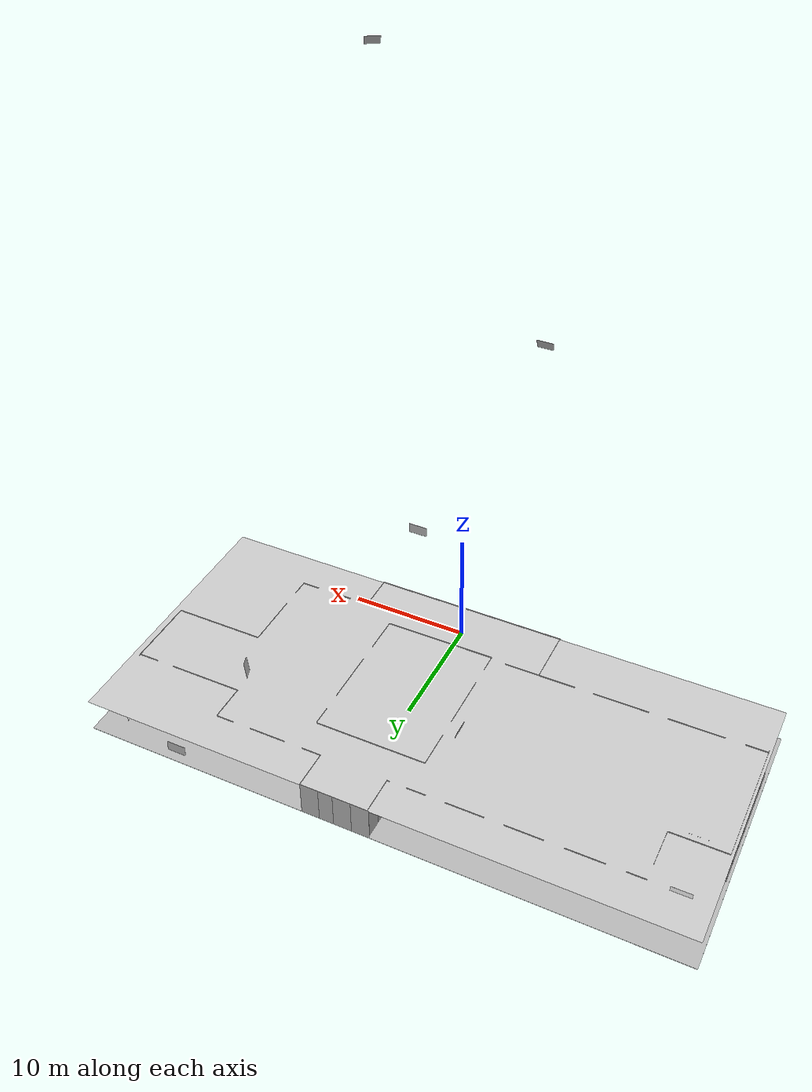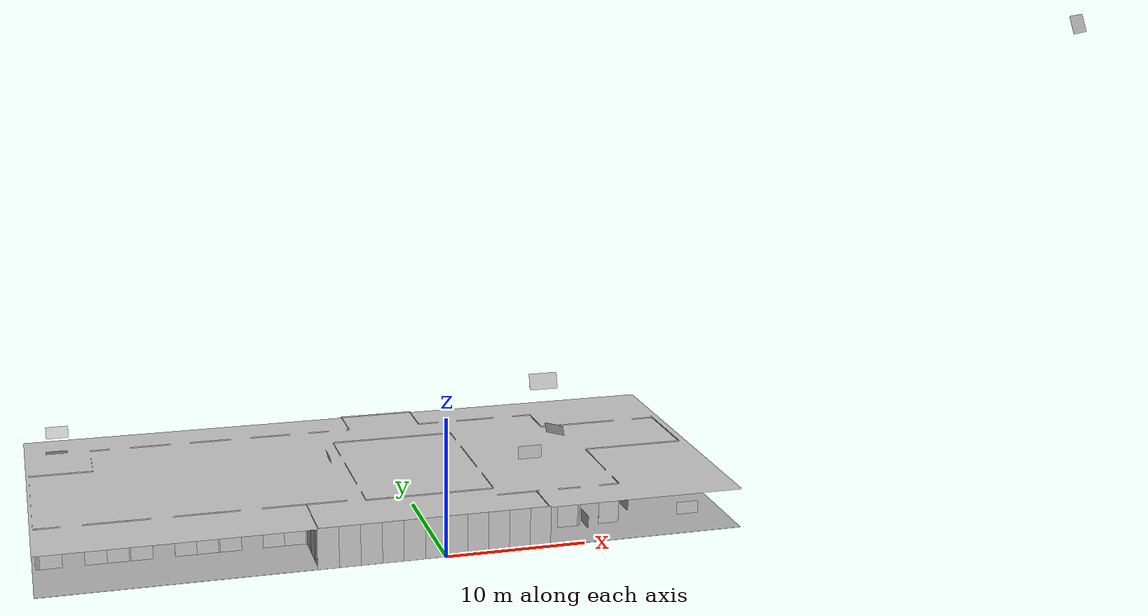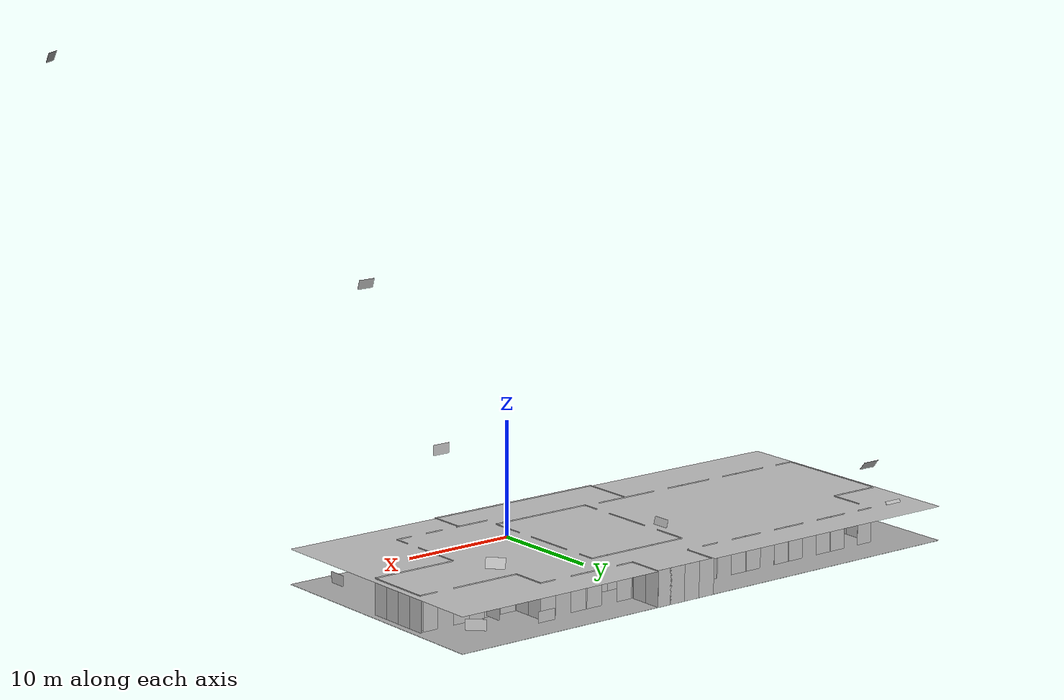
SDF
<sdf version="1.6">
 <world name="default">
  <scene>
   <ambient>0.8 0.8 0.8 1</ambient>
   <background>0.57 0.73 0.85 1</background>
   <grid>0</grid>
   <origin_visual>0</origin_visual>
   <shadows>1</shadows>
  </scene>
  <light name="directional_light" type="directional">
   <pose>0 0 -100 0 -0 0</pose>
   <diffuse>0.5 0.5 0.5 1</diffuse>
   <specular>0.1 0.1 0.1 1</specular>
   <direction>0.1 0.1 -0.9</direction>
   <attenuation>
    <range>20</range>
    <constant>0.5</constant>
    <linear>0.01</linear>
    <quadratic>0.001</quadratic>
   </attenuation>
   <cast_shadows>0</cast_shadows>
  </light>
  <model name="ceiling">
   <pose>-2.97 11.25 3 3.14159 -0 3.14159</pose>
   <static>1</static>
   <link name="link">
    <visual name="visual">
     <geometry><plane><normal>0 0 1</normal><size>49.5 22.5</size></plane></geometry>
     <material>
      <script>
       <uri>file://media/materials/scripts/</uri>
       <uri>file://media/materials/textures/</uri>
       <name>ServiceSim/Ceiling</name>
      </script>
     </material>
    </visual>
   </link>
  </model>
  <model name="floor">
   <pose>-2.97 11.25 -0.001 0 -0 0</pose>
   <static>1</static>
   <link name="link">
    <collision name="collision">
     <geometry><plane><normal>0 0 1</normal><size>49.5 22.5</size></plane></geometry>
     <surface><friction><ode><mu>1</mu><mu2>1</mu2></ode></friction></surface>
    </collision>
    <visual name="visual">
     <geometry><plane><normal>0 0 1</normal><size>49.5 22.5</size></plane></geometry>
     <material>
      <script>
       <uri>file://media/materials/scripts/</uri>
       <uri>file://media/materials/textures/</uri>
       <name>ServiceSim/Hallway</name>
      </script>
     </material>
    </visual>
   </link>
  </model>
  <model name="walls">
   <static>1</static>
   <link name="link">
    <visual name="visual_1">
     <pose>-8.25 0 1.5 0 -0 0</pose>
     <geometry><box><size>1.5 0.01 3</size></box></geometry>
     <material>
      <script>
       <uri>file://media/materials/scripts/</uri>
       <uri>file://media/materials/textures/</uri>
       <name>ServiceSim/PlainWall</name>
      </script>
     </material>
    </visual>
    <visual name="visual_2">
     <pose>-6.75 0 1.5 0 -0 0</pose>
     <geometry><box><size>1.5 0.01 3</size></box></geometry>
     <material>
      <script>
       <uri>file://media/materials/scripts/</uri>
       <uri>file://media/materials/textures/</uri>
       <name>ServiceSim/PlainWall</name>
      </script>
     </material>
    </visual>
    <visual name="visual_3">
     <pose>-5.25 0 1.5 0 -0 0</pose>
     <geometry><box><size>1.5 0.01 3</size></box></geometry>
     <material>
      <script>
       <uri>file://media/materials/scripts/</uri>
       <uri>file://media/materials/textures/</uri>
       <name>ServiceSim/PlainWall</name>
      </script>
     </material>
    </visual>
    <visual name="visual_4">
     <pose>-3.75 0 1.5 0 -0 0</pose>
     <geometry><box><size>1.5 0.01 3</size></box></geometry>
     <material>
      <script>
       <uri>file://media/materials/scripts/</uri>
       <uri>file://media/materials/textures/</uri>
       <name>ServiceSim/PlainWall</name>
      </script>
     </material>
    </visual>
    <visual name="visual_5">
     <pose>-2.25 0 1.5 0 -0 0</pose>
     <geometry><box><size>1.5 0.01 3</size></box></geometry>
     <material>
      <script>
       <uri>file://media/materials/scripts/</uri>
       <uri>file://media/materials/textures/</uri>
       <name>ServiceSim/PlainWall</name>
      </script>
     </material>
    </visual>
    <visual name="visual_6">
     <pose>-0.75 0 1.5 0 -0 0</pose>
     <geometry><box><size>1.5 0.01 3</size></box></geometry>
     <material>
      <script>
       <uri>file://media/materials/scripts/</uri>
       <uri>file://media/materials/textures/</uri>
       <name>ServiceSim/Elevator</name>
      </script>
     </material>
    </visual>
    <visual name="visual_7">
     <pose>0.75 0 1.5 0 -0 0</pose>
     <geometry><box><size>1.5 0.01 3</size></box></geometry>
     <material>
      <script>
       <uri>file://media/materials/scripts/</uri>
       <uri>file://media/materials/textures/</uri>
       <name>ServiceSim/Elevator</name>
      </script>
     </material>
    </visual>
    <visual name="visual_8">
     <pose>2.25 0 1.5 0 -0 0</pose>
     <geometry><box><size>1.5 0.01 3</size></box></geometry>
     <material>
      <script>
       <uri>file://media/materials/scripts/</uri>
       <uri>file://media/materials/textures/</uri>
       <name>ServiceSim/PlainWall</name>
      </script>
     </material>
    </visual>
    <visual name="visual_9">
     <pose>3.75 0 1.5 0 -0 0</pose>
     <geometry><box><size>1.5 0.01 3</size></box></geometry>
     <material>
      <script>
       <uri>file://media/materials/scripts/</uri>
       <uri>file://media/materials/textures/</uri>
       <name>ServiceSim/PlainWall</name>
      </script>
     </material>
    </visual>
    <visual name="visual_10">
     <pose>5.25 0 1.5 0 -0 0</pose>
     <geometry><box><size>1.5 0.01 3</size></box></geometry>
     <material>
      <script>
       <uri>file://media/materials/scripts/</uri>
       <uri>file://media/materials/textures/</uri>
       <name>ServiceSim/PlainWall</name>
      </script>
     </material>
    </visual>
    <visual name="visual_11">
     <pose>6.749 0 1.5 0 -0 0</pose>
     <geometry><box><size>1.5 0.01 3</size></box></geometry>
     <material>
      <script>
       <uri>file://media/materials/scripts/</uri>
       <uri>file://media/materials/textures/</uri>
       <name>ServiceSim/PlainWall</name>
      </script>
     </material>
    </visual>
    <visual name="visual_12">
     <pose>-8.25 4.6 1.5 0 -0 0</pose>
     <geometry><box><size>1.5 0.01 3</size></box></geometry>
     <material>
      <script>
       <uri>file://media/materials/scripts/</uri>
       <uri>file://media/materials/textures/</uri>
       <name>ServiceSim/PlainWall</name>
      </script>
     </material>
    </visual>
    <visual name="visual_13">
     <pose>-6.75 4.6 1.5 0 -0 0</pose>
     <geometry><box><size>1.5 0.01 3</size></box></geometry>
     <material>
      <script>
       <uri>file://media/materials/scripts/</uri>
       <uri>file://media/materials/textures/</uri>
       <name>ServiceSim/PlainWall</name>
      </script>
     </material>
    </visual>
    <visual name="visual_14">
     <pose>5.25 3.1 1.5 0 -0 0</pose>
     <geometry><box><size>1.5 0.01 3</size></box></geometry>
     <material>
      <script>
       <uri>file://media/materials/scripts/</uri>
       <uri>file://media/materials/textures/</uri>
       <name>ServiceSim/PlainWall</name>
      </script>
     </material>
    </visual>
    <visual name="visual_15">
     <pose>6.75 3.1 1.5 0 -0 0</pose>
     <geometry><box><size>1.5 0.01 3</size></box></geometry>
     <material>
      <script>
       <uri>file://media/materials/scripts/</uri>
       <uri>file://media/materials/textures/</uri>
       <name>ServiceSim/PlainWall</name>
      </script>
     </material>
    </visual>
    <visual name="visual_16">
     <pose>7.4 0.75 1.5 0 -0 1.5708</pose>
     <geometry><box><size>1.5 0.01 3</size></box></geometry>
     <material>
      <script>
       <uri>file://media/materials/scripts/</uri>
       <uri>file://media/materials/textures/</uri>
       <name>ServiceSim/PlainWall</name>
      </script>
     </material>
    </visual>
    <visual name="visual_17">
     <pose>7.4 2.25 1.5 0 -0 1.5708</pose>
     <geometry><box><size>1.5 0.01 3</size></box></geometry>
     <material>
      <script>
       <uri>file://media/materials/scripts/</uri>
       <uri>file://media/materials/textures/</uri>
       <name>ServiceSim/PlainWall</name>
      </script>
     </material>
    </visual>
    <visual name="visual_18">
     <pose>7.4 3.05 1.5 0 -0 1.5708</pose>
     <geometry><box><size>0.1 0.01 3</size></box></geometry>
     <material>
      <script>
       <uri>file://media/materials/scripts/</uri>
       <uri>file://media/materials/textures/</uri>
       <name>ServiceSim/PlainWall</name>
      </script>
     </material>
    </visual>
    <visual name="visual_19">
     <pose>7.45 3.1 1.5 0 -0 0</pose>
     <geometry><box><size>0.1 0.01 3</size></box></geometry>
     <material>
      <script>
       <uri>file://media/materials/scripts/</uri>
       <uri>file://media/materials/textures/</uri>
       <name>ServiceSim/PlainWall</name>
      </script>
     </material>
    </visual>
    <visual name="visual_20">
     <pose>7.55 3.1 1.5 0 -0 0</pose>
     <geometry><box><size>0.1 0.01 3</size></box></geometry>
     <material>
      <script>
       <uri>file://media/materials/scripts/</uri>
       <uri>file://media/materials/textures/</uri>
       <name>ServiceSim/PlainWall</name>
      </script>
     </material>
    </visual>
    <visual name="visual_21">
     <pose>9.75 3.1 1.5 0 -0 0</pose>
     <geometry><box><size>1.5 0.01 3</size></box></geometry>
     <material>
      <script>
       <uri>file://media/materials/scripts/</uri>
       <uri>file://media/materials/textures/</uri>
       <name>ServiceSim/PlainWall</name>
      </script>
     </material>
    </visual>
    <visual name="visual_22">
     <pose>10.55 3.1 1.5 0 -0 0</pose>
     <geometry><box><size>0.1 0.01 3</size></box></geometry>
     <material>
      <script>
       <uri>file://media/materials/scripts/</uri>
       <uri>file://media/materials/textures/</uri>
       <name>ServiceSim/PlainWall</name>
      </script>
     </material>
    </visual>
    <visual name="visual_23">
     <pose>10.65 3.1 1.5 0 -0 0</pose>
     <geometry><box><size>0.1 0.01 3</size></box></geometry>
     <material>
      <script>
       <uri>file://media/materials/scripts/</uri>
       <uri>file://media/materials/textures/</uri>
       <name>ServiceSim/PlainWall</name>
      </script>
     </material>
    </visual>
    <visual name="visual_24">
     <pose>12.85 3.1 1.5 0 -0 0</pose>
     <geometry><box><size>1.5 0.01 3</size></box></geometry>
     <material>
      <script>
       <uri>file://media/materials/scripts/</uri>
       <uri>file://media/materials/textures/</uri>
       <name>ServiceSim/PlainWall</name>
      </script>
     </material>
    </visual>
    <visual name="visual_25">
     <pose>13.6 3.85 1.5 0 -0 1.5708</pose>
     <geometry><box><size>1.5 0.01 3</size></box></geometry>
     <material>
      <script>
       <uri>file://media/materials/scripts/</uri>
       <uri>file://media/materials/textures/</uri>
       <name>ServiceSim/PlainWall</name>
      </script>
     </material>
    </visual>
    <visual name="visual_26">
     <pose>13.6 6.75 1.5 0 -0 1.5708</pose>
     <geometry><box><size>1.5 0.01 3</size></box></geometry>
     <material>
      <script>
       <uri>file://media/materials/scripts/</uri>
       <uri>file://media/materials/textures/</uri>
       <name>ServiceSim/PlainWall</name>
      </script>
     </material>
    </visual>
    <visual name="visual_27">
     <pose>13.6 8.25 1.5 0 -0 1.5708</pose>
     <geometry><box><size>1.5 0.01 3</size></box></geometry>
     <material>
      <script>
       <uri>file://media/materials/scripts/</uri>
       <uri>file://media/materials/textures/</uri>
       <name>ServiceSim/PlainWall</name>
      </script>
     </material>
    </visual>
    <visual name="visual_28">
     <pose>13.6 9.75 1.5 0 -0 1.5708</pose>
     <geometry><box><size>1.5 0.01 3</size></box></geometry>
     <material>
      <script>
       <uri>file://media/materials/scripts/</uri>
       <uri>file://media/materials/textures/</uri>
       <name>ServiceSim/PlainWall</name>
      </script>
     </material>
    </visual>
    <visual name="visual_29">
     <pose>13.6 10.55 1.5 0 -0 1.5708</pose>
     <geometry><box><size>0.1 0.01 3</size></box></geometry>
     <material>
      <script>
       <uri>file://media/materials/scripts/</uri>
       <uri>file://media/materials/textures/</uri>
       <name>ServiceSim/PlainWall</name>
      </script>
     </material>
    </visual>
    <visual name="visual_30">
     <pose>14.35 10.6 1.5 0 -0 0</pose>
     <geometry><box><size>1.5 0.01 3</size></box></geometry>
     <material>
      <script>
       <uri>file://media/materials/scripts/</uri>
       <uri>file://media/materials/textures/</uri>
       <name>ServiceSim/PlainWall</name>
      </script>
     </material>
    </visual>
    <visual name="visual_31">
     <pose>15.85 10.6 1.5 0 -0 0</pose>
     <geometry><box><size>1.5 0.01 3</size></box></geometry>
     <material>
      <script>
       <uri>file://media/materials/scripts/</uri>
       <uri>file://media/materials/textures/</uri>
       <name>ServiceSim/PlainWall</name>
      </script>
     </material>
    </visual>
    <visual name="visual_32">
     <pose>17.35 10.6 1.5 0 -0 0</pose>
     <geometry><box><size>1.5 0.01 3</size></box></geometry>
     <material>
      <script>
       <uri>file://media/materials/scripts/</uri>
       <uri>file://media/materials/textures/</uri>
       <name>ServiceSim/PlainWall</name>
      </script>
     </material>
    </visual>
    <visual name="visual_33">
     <pose>18.85 10.6 1.5 0 -0 0</pose>
     <geometry><box><size>1.5 0.01 3</size></box></geometry>
     <material>
      <script>
       <uri>file://media/materials/scripts/</uri>
       <uri>file://media/materials/textures/</uri>
       <name>ServiceSim/PlainWall</name>
      </script>
     </material>
    </visual>
    <visual name="visual_34">
     <pose>20.35 10.6 1.5 0 -0 0</pose>
     <geometry><box><size>1.5 0.01 3</size></box></geometry>
     <material>
      <script>
       <uri>file://media/materials/scripts/</uri>
       <uri>file://media/materials/textures/</uri>
       <name>ServiceSim/PlainWall</name>
      </script>
     </material>
    </visual>
    <visual name="visual_35">
     <pose>21.15 10.6 1.5 0 -0 0</pose>
     <geometry><box><size>0.1 0.01 3</size></box></geometry>
     <material>
      <script>
       <uri>file://media/materials/scripts/</uri>
       <uri>file://media/materials/textures/</uri>
       <name>ServiceSim/PlainWall</name>
      </script>
     </material>
    </visual>
    <visual name="visual_36">
     <pose>21.2 11.35 1.5 0 -0 1.5708</pose>
     <geometry><box><size>1.5 0.01 3</size></box></geometry>
     <material>
      <script>
       <uri>file://media/materials/scripts/</uri>
       <uri>file://media/materials/textures/</uri>
       <name>ServiceSim/PlainWall</name>
      </script>
     </material>
    </visual>
    <visual name="visual_37">
     <pose>21.2 12.85 1.5 0 -0 1.5708</pose>
     <geometry><box><size>1.5 0.01 3</size></box></geometry>
     <material>
      <script>
       <uri>file://media/materials/scripts/</uri>
       <uri>file://media/materials/textures/</uri>
       <name>ServiceSim/PlainWall</name>
      </script>
     </material>
    </visual>
    <visual name="visual_38">
     <pose>21.2 14.35 1.5 0 -0 1.5708</pose>
     <geometry><box><size>1.5 0.01 3</size></box></geometry>
     <material>
      <script>
       <uri>file://media/materials/scripts/</uri>
       <uri>file://media/materials/textures/</uri>
       <name>ServiceSim/PlainWall</name>
      </script>
     </material>
    </visual>
    <visual name="visual_39">
     <pose>21.2 15.85 1.5 0 -0 1.5708</pose>
     <geometry><box><size>1.5 0.01 3</size></box></geometry>
     <material>
      <script>
       <uri>file://media/materials/scripts/</uri>
       <uri>file://media/materials/textures/</uri>
       <name>ServiceSim/PlainWall</name>
      </script>
     </material>
    </visual>
    <visual name="visual_40">
     <pose>20.95 16.4 1.5 0 -0 0</pose>
     <geometry><box><size>0.1 0.01 3</size></box></geometry>
     <material>
      <script>
       <uri>file://media/materials/scripts/</uri>
       <uri>file://media/materials/textures/</uri>
       <name>ServiceSim/PlainWall</name>
      </script>
     </material>
    </visual>
    <visual name="visual_41">
     <pose>21.05 16.4 1.5 0 -0 0</pose>
     <geometry><box><size>0.1 0.01 3</size></box></geometry>
     <material>
      <script>
       <uri>file://media/materials/scripts/</uri>
       <uri>file://media/materials/textures/</uri>
       <name>ServiceSim/PlainWall</name>
      </script>
     </material>
    </visual>
    <visual name="visual_42">
     <pose>21.15 16.4 1.5 0 -0 0</pose>
     <geometry><box><size>0.1 0.01 3</size></box></geometry>
     <material>
      <script>
       <uri>file://media/materials/scripts/</uri>
       <uri>file://media/materials/textures/</uri>
       <name>ServiceSim/PlainWall</name>
      </script>
     </material>
    </visual>
    <visual name="visual_43">
     <pose>20.25 16.4 1.5 0 -0 0</pose>
     <geometry><box><size>1.5 0.01 3</size></box></geometry>
     <material>
      <script>
       <uri>file://media/materials/scripts/</uri>
       <uri>file://media/materials/textures/</uri>
       <name>ServiceSim/PlainWall</name>
      </script>
     </material>
    </visual>
    <visual name="visual_44">
     <pose>17.25 16.4 1.5 0 -0 0</pose>
     <geometry><box><size>1.5 0.01 3</size></box></geometry>
     <material>
      <script>
       <uri>file://media/materials/scripts/</uri>
       <uri>file://media/materials/textures/</uri>
       <name>ServiceSim/PlainWall</name>
      </script>
     </material>
    </visual>
    <visual name="visual_45">
     <pose>15.75 16.4 1.5 0 -0 0</pose>
     <geometry><box><size>1.5 0.01 3</size></box></geometry>
     <material>
      <script>
       <uri>file://media/materials/scripts/</uri>
       <uri>file://media/materials/textures/</uri>
       <name>ServiceSim/PlainWall</name>
      </script>
     </material>
    </visual>
    <visual name="visual_46">
     <pose>14.25 16.4 1.5 0 -0 0</pose>
     <geometry><box><size>1.5 0.01 3</size></box></geometry>
     <material>
      <script>
       <uri>file://media/materials/scripts/</uri>
       <uri>file://media/materials/textures/</uri>
       <name>ServiceSim/PlainWall</name>
      </script>
     </material>
    </visual>
    <visual name="visual_47">
     <pose>12.75 16.4 1.5 0 -0 0</pose>
     <geometry><box><size>1.5 0.01 3</size></box></geometry>
     <material>
      <script>
       <uri>file://media/materials/scripts/</uri>
       <uri>file://media/materials/textures/</uri>
       <name>ServiceSim/PlainWall</name>
      </script>
     </material>
    </visual>
    <visual name="visual_48">
     <pose>11.95 16.4 1.5 0 -0 0</pose>
     <geometry><box><size>0.1 0.01 3</size></box></geometry>
     <material>
      <script>
       <uri>file://media/materials/scripts/</uri>
       <uri>file://media/materials/textures/</uri>
       <name>ServiceSim/PlainWall</name>
      </script>
     </material>
    </visual>
    <visual name="visual_49">
     <pose>11.9 17.15 1.5 0 -0 1.5708</pose>
     <geometry><box><size>1.5 0.01 3</size></box></geometry>
     <material>
      <script>
       <uri>file://media/materials/scripts/</uri>
       <uri>file://media/materials/textures/</uri>
       <name>ServiceSim/PlainWall</name>
      </script>
     </material>
    </visual>
    <visual name="visual_50">
     <pose>11.9 18.65 1.5 0 -0 1.5708</pose>
     <geometry><box><size>1.5 0.01 3</size></box></geometry>
     <material>
      <script>
       <uri>file://media/materials/scripts/</uri>
       <uri>file://media/materials/textures/</uri>
       <name>ServiceSim/PlainWall</name>
      </script>
     </material>
    </visual>
    <visual name="visual_51">
     <pose>11.15 19.4 1.5 0 -0 0</pose>
     <geometry><box><size>1.5 0.01 3</size></box></geometry>
     <material>
      <script>
       <uri>file://media/materials/scripts/</uri>
       <uri>file://media/materials/textures/</uri>
       <name>ServiceSim/PlainWall</name>
      </script>
     </material>
    </visual>
    <visual name="visual_52">
     <pose>8.15 19.4 1.5 0 -0 0</pose>
     <geometry><box><size>1.5 0.01 3</size></box></geometry>
     <material>
      <script>
       <uri>file://media/materials/scripts/</uri>
       <uri>file://media/materials/textures/</uri>
       <name>ServiceSim/PlainWall</name>
      </script>
     </material>
    </visual>
    <visual name="visual_53">
     <pose>7.35 19.4 1.5 0 -0 0</pose>
     <geometry><box><size>0.1 0.01 3</size></box></geometry>
     <material>
      <script>
       <uri>file://media/materials/scripts/</uri>
       <uri>file://media/materials/textures/</uri>
       <name>ServiceSim/PlainWall</name>
      </script>
     </material>
    </visual>
    <visual name="visual_54">
     <pose>6.55 19.4 1.5 0 -0 0</pose>
     <geometry><box><size>1.5 0.01 3</size></box></geometry>
     <material>
      <script>
       <uri>file://media/materials/scripts/</uri>
       <uri>file://media/materials/textures/</uri>
       <name>ServiceSim/PlainWall</name>
      </script>
     </material>
    </visual>
    <visual name="visual_55">
     <pose>3.55 19.4 1.5 0 -0 0</pose>
     <geometry><box><size>1.5 0.01 3</size></box></geometry>
     <material>
      <script>
       <uri>file://media/materials/scripts/</uri>
       <uri>file://media/materials/textures/</uri>
       <name>ServiceSim/PlainWall</name>
      </script>
     </material>
    </visual>
    <visual name="visual_56">
     <pose>2.75 19.4 1.5 0 -0 0</pose>
     <geometry><box><size>0.1 0.01 3</size></box></geometry>
     <material>
      <script>
       <uri>file://media/materials/scripts/</uri>
       <uri>file://media/materials/textures/</uri>
       <name>ServiceSim/PlainWall</name>
      </script>
     </material>
    </visual>
    <visual name="visual_57">
     <pose>2.7 19.45 1.5 0 -0 1.5708</pose>
     <geometry><box><size>0.1 0.01 3</size></box></geometry>
     <material>
      <script>
       <uri>file://media/materials/scripts/</uri>
       <uri>file://media/materials/textures/</uri>
       <name>ServiceSim/PlainWall</name>
      </script>
     </material>
    </visual>
    <visual name="visual_58">
     <pose>2.7 20.25 1.5 0 -0 1.5708</pose>
     <geometry><box><size>1.5 0.01 3</size></box></geometry>
     <material>
      <script>
       <uri>file://media/materials/scripts/</uri>
       <uri>file://media/materials/textures/</uri>
       <name>ServiceSim/PlainWall</name>
      </script>
     </material>
    </visual>
    <visual name="visual_59">
     <pose>2.7 21.75 1.5 0 -0 1.5708</pose>
     <geometry><box><size>1.5 0.01 3</size></box></geometry>
     <material>
      <script>
       <uri>file://media/materials/scripts/</uri>
       <uri>file://media/materials/textures/</uri>
       <name>ServiceSim/PlainWall</name>
      </script>
     </material>
    </visual>
    <visual name="visual_60">
     <pose>1.95 22.5 1.5 0 -0 0</pose>
     <geometry><box><size>1.5 0.01 3</size></box></geometry>
     <material>
      <script>
       <uri>file://media/materials/scripts/</uri>
       <uri>file://media/materials/textures/</uri>
       <name>ServiceSim/PlainWall</name>
      </script>
     </material>
    </visual>
    <visual name="visual_61">
     <pose>0.75 22.5 1.5 0 -0 0</pose>
     <geometry><box><size>1.5 0.01 3</size></box></geometry>
     <material>
      <script>
       <uri>file://media/materials/scripts/</uri>
       <uri>file://media/materials/textures/</uri>
       <name>ServiceSim/PlainWall</name>
      </script>
     </material>
    </visual>
    <visual name="visual_62">
     <pose>-0.75 22.5 1.5 0 -0 0</pose>
     <geometry><box><size>1.5 0.01 3</size></box></geometry>
     <material>
      <script>
       <uri>file://media/materials/scripts/</uri>
       <uri>file://media/materials/textures/</uri>
       <name>ServiceSim/PlainWall</name>
      </script>
     </material>
    </visual>
    <visual name="visual_63">
     <pose>-2.25 22.5 1.5 0 -0 0</pose>
     <geometry><box><size>1.5 0.01 3</size></box></geometry>
     <material>
      <script>
       <uri>file://media/materials/scripts/</uri>
       <uri>file://media/materials/textures/</uri>
       <name>ServiceSim/Door</name>
      </script>
     </material>
    </visual>
    <visual name="visual_64">
     <pose>-2.9 21.75 1.5 0 -0 1.5708</pose>
     <geometry><box><size>1.5 0.01 3</size></box></geometry>
     <material>
      <script>
       <uri>file://media/materials/scripts/</uri>
       <uri>file://media/materials/textures/</uri>
       <name>ServiceSim/PlainWall</name>
      </script>
     </material>
    </visual>
    <visual name="visual_65">
     <pose>-2.9 20.25 1.5 0 -0 1.5708</pose>
     <geometry><box><size>1.5 0.01 3</size></box></geometry>
     <material>
      <script>
       <uri>file://media/materials/scripts/</uri>
       <uri>file://media/materials/textures/</uri>
       <name>ServiceSim/PlainWall</name>
      </script>
     </material>
    </visual>
    <visual name="visual_66">
     <pose>-2.9 19.45 1.5 0 -0 1.5708</pose>
     <geometry><box><size>0.1 0.01 3</size></box></geometry>
     <material>
      <script>
       <uri>file://media/materials/scripts/</uri>
       <uri>file://media/materials/textures/</uri>
       <name>ServiceSim/PlainWall</name>
      </script>
     </material>
    </visual>
    <visual name="visual_67">
     <pose>-2.95 19.4 1.5 0 -0 0</pose>
     <geometry><box><size>0.1 0.01 3</size></box></geometry>
     <material>
      <script>
       <uri>file://media/materials/scripts/</uri>
       <uri>file://media/materials/textures/</uri>
       <name>ServiceSim/PlainWall</name>
      </script>
     </material>
    </visual>
    <visual name="visual_68">
     <pose>-3.05 19.4 1.5 0 -0 0</pose>
     <geometry><box><size>0.1 0.01 3</size></box></geometry>
     <material>
      <script>
       <uri>file://media/materials/scripts/</uri>
       <uri>file://media/materials/textures/</uri>
       <name>ServiceSim/PlainWall</name>
      </script>
     </material>
    </visual>
    <visual name="visual_69">
     <pose>-5.25 19.4 1.5 0 -0 0</pose>
     <geometry><box><size>1.5 0.01 3</size></box></geometry>
     <material>
      <script>
       <uri>file://media/materials/scripts/</uri>
       <uri>file://media/materials/textures/</uri>
       <name>ServiceSim/PlainWall</name>
      </script>
     </material>
    </visual>
    <visual name="visual_70">
     <pose>-6.05 19.4 1.5 0 -0 0</pose>
     <geometry><box><size>0.1 0.01 3</size></box></geometry>
     <material>
      <script>
       <uri>file://media/materials/scripts/</uri>
       <uri>file://media/materials/textures/</uri>
       <name>ServiceSim/PlainWall</name>
      </script>
     </material>
    </visual>
    <visual name="visual_71">
     <pose>-8.35 19.4 1.5 0 -0 0</pose>
     <geometry><box><size>1.5 0.01 3</size></box></geometry>
     <material>
      <script>
       <uri>file://media/materials/scripts/</uri>
       <uri>file://media/materials/textures/</uri>
       <name>ServiceSim/PlainWall</name>
      </script>
     </material>
    </visual>
    <visual name="visual_72">
     <pose>-9.15 19.4 1.5 0 -0 0</pose>
     <geometry><box><size>0.1 0.01 3</size></box></geometry>
     <material>
      <script>
       <uri>file://media/materials/scripts/</uri>
       <uri>file://media/materials/textures/</uri>
       <name>ServiceSim/PlainWall</name>
      </script>
     </material>
    </visual>
    <visual name="visual_73">
     <pose>-9.95 19.4 1.5 0 -0 0</pose>
     <geometry><box><size>1.5 0.01 3</size></box></geometry>
     <material>
      <script>
       <uri>file://media/materials/scripts/</uri>
       <uri>file://media/materials/textures/</uri>
       <name>ServiceSim/PlainWall</name>
      </script>
     </material>
    </visual>
    <visual name="visual_74">
     <pose>-12.95 19.4 1.5 0 -0 0</pose>
     <geometry><box><size>1.5 0.01 3</size></box></geometry>
     <material>
      <script>
       <uri>file://media/materials/scripts/</uri>
       <uri>file://media/materials/textures/</uri>
       <name>ServiceSim/PlainWall</name>
      </script>
     </material>
    </visual>
    <visual name="visual_75">
     <pose>-13.75 19.4 1.5 0 -0 0</pose>
     <geometry><box><size>0.1 0.01 3</size></box></geometry>
     <material>
      <script>
       <uri>file://media/materials/scripts/</uri>
       <uri>file://media/materials/textures/</uri>
       <name>ServiceSim/PlainWall</name>
      </script>
     </material>
    </visual>
    <visual name="visual_76">
     <pose>-14.55 19.4 1.5 0 -0 0</pose>
     <geometry><box><size>1.5 0.01 3</size></box></geometry>
     <material>
      <script>
       <uri>file://media/materials/scripts/</uri>
       <uri>file://media/materials/textures/</uri>
       <name>ServiceSim/PlainWall</name>
      </script>
     </material>
    </visual>
    <visual name="visual_77">
     <pose>-18.35 19.4 1.5 0 -0 0</pose>
     <geometry><box><size>0.1 0.01 3</size></box></geometry>
     <material>
      <script>
       <uri>file://media/materials/scripts/</uri>
       <uri>file://media/materials/textures/</uri>
       <name>ServiceSim/PlainWall</name>
      </script>
     </material>
    </visual>
    <visual name="visual_78">
     <pose>-17.55 19.4 1.5 0 -0 0</pose>
     <geometry><box><size>1.5 0.01 3</size></box></geometry>
     <material>
      <script>
       <uri>file://media/materials/scripts/</uri>
       <uri>file://media/materials/textures/</uri>
       <name>ServiceSim/PlainWall</name>
      </script>
     </material>
    </visual>
    <visual name="visual_79">
     <pose>-19.15 19.4 1.5 0 -0 0</pose>
     <geometry><box><size>1.5 0.01 3</size></box></geometry>
     <material>
      <script>
       <uri>file://media/materials/scripts/</uri>
       <uri>file://media/materials/textures/</uri>
       <name>ServiceSim/PlainWall</name>
      </script>
     </material>
    </visual>
    <visual name="visual_80">
     <pose>-22.15 19.4 1.5 0 -0 0</pose>
     <geometry><box><size>1.5 0.01 3</size></box></geometry>
     <material>
      <script>
       <uri>file://media/materials/scripts/</uri>
       <uri>file://media/materials/textures/</uri>
       <name>ServiceSim/PlainWall</name>
      </script>
     </material>
    </visual>
    <visual name="visual_81">
     <pose>-22.9 17.25 1.5 0 -0 1.5708</pose>
     <geometry><box><size>1.5 0.01 3</size></box></geometry>
     <material>
      <script>
       <uri>file://media/materials/scripts/</uri>
       <uri>file://media/materials/textures/</uri>
       <name>ServiceSim/PlainWall</name>
      </script>
     </material>
    </visual>
    <visual name="visual_82">
     <pose>-22.9 15.75 1.5 0 -0 1.5708</pose>
     <geometry><box><size>1.5 0.01 3</size></box></geometry>
     <material>
      <script>
       <uri>file://media/materials/scripts/</uri>
       <uri>file://media/materials/textures/</uri>
       <name>ServiceSim/PlainWall</name>
      </script>
     </material>
    </visual>
    <visual name="visual_83">
     <pose>-22.9 14.95 1.5 0 -0 1.5708</pose>
     <geometry><box><size>0.1 0.01 3</size></box></geometry>
     <material>
      <script>
       <uri>file://media/materials/scripts/</uri>
       <uri>file://media/materials/textures/</uri>
       <name>ServiceSim/PlainWall</name>
      </script>
     </material>
    </visual>
    <visual name="visual_84">
     <pose>-22.95 14.9 1.5 0 -0 0</pose>
     <geometry><box><size>0.1 0.01 3</size></box></geometry>
     <material>
      <script>
       <uri>file://media/materials/scripts/</uri>
       <uri>file://media/materials/textures/</uri>
       <name>ServiceSim/PlainWall</name>
      </script>
     </material>
    </visual>
    <visual name="visual_85">
     <pose>-23.75 14.9 1.5 0 -0 0</pose>
     <geometry><box><size>1.5 0.01 3</size></box></geometry>
     <material>
      <script>
       <uri>file://media/materials/scripts/</uri>
       <uri>file://media/materials/textures/</uri>
       <name>ServiceSim/PlainWall</name>
      </script>
     </material>
    </visual>
    <visual name="visual_86">
     <pose>-25.25 14.9 1.5 0 -0 0</pose>
     <geometry><box><size>1.5 0.01 3</size></box></geometry>
     <material>
      <script>
       <uri>file://media/materials/scripts/</uri>
       <uri>file://media/materials/textures/</uri>
       <name>ServiceSim/PlainWall</name>
      </script>
     </material>
    </visual>
    <visual name="visual_87">
     <pose>-26.75 14.9 1.5 0 -0 0</pose>
     <geometry><box><size>1.5 0.01 3</size></box></geometry>
     <material>
      <script>
       <uri>file://media/materials/scripts/</uri>
       <uri>file://media/materials/textures/</uri>
       <name>ServiceSim/PlainWall</name>
      </script>
     </material>
    </visual>
    <visual name="visual_88">
     <pose>-27.5 14.15 1.5 0 -0 1.5708</pose>
     <geometry><box><size>1.5 0.01 3</size></box></geometry>
     <material>
      <script>
       <uri>file://media/materials/scripts/</uri>
       <uri>file://media/materials/textures/</uri>
       <name>ServiceSim/PlainWall</name>
      </script>
     </material>
    </visual>
    <visual name="visual_89">
     <pose>-27.5 12.65 1.5 0 -0 1.5708</pose>
     <geometry><box><size>1.5 0.01 3</size></box></geometry>
     <material>
      <script>
       <uri>file://media/materials/scripts/</uri>
       <uri>file://media/materials/textures/</uri>
       <name>ServiceSim/PlainWall</name>
      </script>
     </material>
    </visual>
    <visual name="visual_90">
     <pose>-27.5 11.15 1.5 0 -0 1.5708</pose>
     <geometry><box><size>1.5 0.01 3</size></box></geometry>
     <material>
      <script>
       <uri>file://media/materials/scripts/</uri>
       <uri>file://media/materials/textures/</uri>
       <name>ServiceSim/PlainWall</name>
      </script>
     </material>
    </visual>
    <visual name="visual_91">
     <pose>-27.5 9.65 1.5 0 -0 1.5708</pose>
     <geometry><box><size>1.5 0.01 3</size></box></geometry>
     <material>
      <script>
       <uri>file://media/materials/scripts/</uri>
       <uri>file://media/materials/textures/</uri>
       <name>ServiceSim/PlainWall</name>
      </script>
     </material>
    </visual>
    <visual name="visual_92">
     <pose>-27.5 8.15 1.5 0 -0 1.5708</pose>
     <geometry><box><size>1.5 0.01 3</size></box></geometry>
     <material>
      <script>
       <uri>file://media/materials/scripts/</uri>
       <uri>file://media/materials/textures/</uri>
       <name>ServiceSim/PlainWall</name>
      </script>
     </material>
    </visual>
    <visual name="visual_93">
     <pose>-27.5 6.65 1.5 0 -0 1.5708</pose>
     <geometry><box><size>1.5 0.01 3</size></box></geometry>
     <material>
      <script>
       <uri>file://media/materials/scripts/</uri>
       <uri>file://media/materials/textures/</uri>
       <name>ServiceSim/PlainWall</name>
      </script>
     </material>
    </visual>
    <visual name="visual_94">
     <pose>-27.5 5.15 1.5 0 -0 1.5708</pose>
     <geometry><box><size>1.5 0.01 3</size></box></geometry>
     <material>
      <script>
       <uri>file://media/materials/scripts/</uri>
       <uri>file://media/materials/textures/</uri>
       <name>ServiceSim/PlainWall</name>
      </script>
     </material>
    </visual>
    <visual name="visual_95">
     <pose>-27.45 4.6 1.5 0 -0 0</pose>
     <geometry><box><size>0.1 0.01 3</size></box></geometry>
     <material>
      <script>
       <uri>file://media/materials/scripts/</uri>
       <uri>file://media/materials/textures/</uri>
       <name>ServiceSim/PlainWall</name>
      </script>
     </material>
    </visual>
    <visual name="visual_96">
     <pose>-27.35 4.6 1.5 0 -0 0</pose>
     <geometry><box><size>0.1 0.01 3</size></box></geometry>
     <material>
      <script>
       <uri>file://media/materials/scripts/</uri>
       <uri>file://media/materials/textures/</uri>
       <name>ServiceSim/PlainWall</name>
      </script>
     </material>
    </visual>
    <visual name="visual_97">
     <pose>-27.25 4.6 1.5 0 -0 0</pose>
     <geometry><box><size>0.1 0.01 3</size></box></geometry>
     <material>
      <script>
       <uri>file://media/materials/scripts/</uri>
       <uri>file://media/materials/textures/</uri>
       <name>ServiceSim/PlainWall</name>
      </script>
     </material>
    </visual>
    <visual name="visual_98">
     <pose>-26.45 4.6 1.5 0 -0 0</pose>
     <geometry><box><size>1.5 0.01 3</size></box></geometry>
     <material>
      <script>
       <uri>file://media/materials/scripts/</uri>
       <uri>file://media/materials/textures/</uri>
       <name>ServiceSim/PlainWall</name>
      </script>
     </material>
    </visual>
    <visual name="visual_99">
     <pose>-23.45 4.6 1.5 0 -0 0</pose>
     <geometry><box><size>1.5 0.01 3</size></box></geometry>
     <material>
      <script>
       <uri>file://media/materials/scripts/</uri>
       <uri>file://media/materials/textures/</uri>
       <name>ServiceSim/PlainWall</name>
      </script>
     </material>
    </visual>
    <visual name="visual_100">
     <pose>-21.95 4.6 1.5 0 -0 0</pose>
     <geometry><box><size>1.5 0.01 3</size></box></geometry>
     <material>
      <script>
       <uri>file://media/materials/scripts/</uri>
       <uri>file://media/materials/textures/</uri>
       <name>ServiceSim/PlainWall</name>
      </script>
     </material>
    </visual>
    <visual name="visual_101">
     <pose>-21.15 4.6 1.5 0 -0 0</pose>
     <geometry><box><size>0.1 0.01 3</size></box></geometry>
     <material>
      <script>
       <uri>file://media/materials/scripts/</uri>
       <uri>file://media/materials/textures/</uri>
       <name>ServiceSim/PlainWall</name>
      </script>
     </material>
    </visual>
    <visual name="visual_102">
     <pose>-20.35 4.6 1.5 0 -0 0</pose>
     <geometry><box><size>1.5 0.01 3</size></box></geometry>
     <material>
      <script>
       <uri>file://media/materials/scripts/</uri>
       <uri>file://media/materials/textures/</uri>
       <name>ServiceSim/PlainWall</name>
      </script>
     </material>
    </visual>
    <visual name="visual_103">
     <pose>-17.35 4.6 1.5 0 -0 0</pose>
     <geometry><box><size>1.5 0.01 3</size></box></geometry>
     <material>
      <script>
       <uri>file://media/materials/scripts/</uri>
       <uri>file://media/materials/textures/</uri>
       <name>ServiceSim/PlainWall</name>
      </script>
     </material>
    </visual>
    <visual name="visual_104">
     <pose>-15.85 4.6 1.5 0 -0 0</pose>
     <geometry><box><size>1.5 0.01 3</size></box></geometry>
     <material>
      <script>
       <uri>file://media/materials/scripts/</uri>
       <uri>file://media/materials/textures/</uri>
       <name>ServiceSim/PlainWall</name>
      </script>
     </material>
    </visual>
    <visual name="visual_105">
     <pose>-15.05 4.6 1.5 0 -0 0</pose>
     <geometry><box><size>0.1 0.01 3</size></box></geometry>
     <material>
      <script>
       <uri>file://media/materials/scripts/</uri>
       <uri>file://media/materials/textures/</uri>
       <name>ServiceSim/PlainWall</name>
      </script>
     </material>
    </visual>
    <visual name="visual_106">
     <pose>-14.25 4.6 1.5 0 -0 0</pose>
     <geometry><box><size>1.5 0.01 3</size></box></geometry>
     <material>
      <script>
       <uri>file://media/materials/scripts/</uri>
       <uri>file://media/materials/textures/</uri>
       <name>ServiceSim/PlainWall</name>
      </script>
     </material>
    </visual>
    <visual name="visual_107">
     <pose>-11.25 4.6 1.5 0 -0 0</pose>
     <geometry><box><size>1.5 0.01 3</size></box></geometry>
     <material>
      <script>
       <uri>file://media/materials/scripts/</uri>
       <uri>file://media/materials/textures/</uri>
       <name>ServiceSim/PlainWall</name>
      </script>
     </material>
    </visual>
    <visual name="visual_108">
     <pose>-9.75 4.6 1.5 0 -0 0</pose>
     <geometry><box><size>1.5 0.01 3</size></box></geometry>
     <material>
      <script>
       <uri>file://media/materials/scripts/</uri>
       <uri>file://media/materials/textures/</uri>
       <name>ServiceSim/PlainWall</name>
      </script>
     </material>
    </visual>
    <visual name="visual_109">
     <pose>-8.95 4.6 1.5 0 -0 0</pose>
     <geometry><box><size>0.1 0.01 3</size></box></geometry>
     <material>
      <script>
       <uri>file://media/materials/scripts/</uri>
       <uri>file://media/materials/textures/</uri>
       <name>ServiceSim/PlainWall</name>
      </script>
     </material>
    </visual>
    <visual name="visual_110">
     <pose>-8.9 4.55 1.5 0 -0 1.5708</pose>
     <geometry><box><size>0.1 0.01 3</size></box></geometry>
     <material>
      <script>
       <uri>file://media/materials/scripts/</uri>
       <uri>file://media/materials/textures/</uri>
       <name>ServiceSim/PlainWall</name>
      </script>
     </material>
    </visual>
    <visual name="visual_111">
     <pose>-8.9 3.75 1.5 0 -0 1.5708</pose>
     <geometry><box><size>1.5 0.01 3</size></box></geometry>
     <material>
      <script>
       <uri>file://media/materials/scripts/</uri>
       <uri>file://media/materials/textures/</uri>
       <name>ServiceSim/PlainWall</name>
      </script>
     </material>
    </visual>
    <visual name="visual_112">
     <pose>-8.9 2.25 1.5 0 -0 1.5708</pose>
     <geometry><box><size>1.5 0.01 3</size></box></geometry>
     <material>
      <script>
       <uri>file://media/materials/scripts/</uri>
       <uri>file://media/materials/textures/</uri>
       <name>ServiceSim/PlainWall</name>
      </script>
     </material>
    </visual>
    <visual name="visual_113">
     <pose>-8.9 0.75 1.5 0 -0 1.5708</pose>
     <geometry><box><size>1.5 0.01 3</size></box></geometry>
     <material>
      <script>
       <uri>file://media/materials/scripts/</uri>
       <uri>file://media/materials/textures/</uri>
       <name>ServiceSim/PlainWall</name>
      </script>
     </material>
    </visual>
    <visual name="visual_114">
     <pose>-4.65 4.4 1.5 0 -0 0</pose>
     <geometry><box><size>0.1 0.01 3</size></box></geometry>
     <material>
      <script>
       <uri>file://media/materials/scripts/</uri>
       <uri>file://media/materials/textures/</uri>
       <name>ServiceSim/PlainWall</name>
      </script>
     </material>
    </visual>
    <visual name="visual_115">
     <pose>-3.85 4.4 1.5 0 -0 0</pose>
     <geometry><box><size>1.5 0.01 3</size></box></geometry>
     <material>
      <script>
       <uri>file://media/materials/scripts/</uri>
       <uri>file://media/materials/textures/</uri>
       <name>ServiceSim/PlainWall</name>
      </script>
     </material>
    </visual>
    <visual name="visual_116">
     <pose>-2.35 4.4 1.5 0 -0 0</pose>
     <geometry><box><size>1.5 0.01 3</size></box></geometry>
     <material>
      <script>
       <uri>file://media/materials/scripts/</uri>
       <uri>file://media/materials/textures/</uri>
       <name>ServiceSim/PlainWall</name>
      </script>
     </material>
    </visual>
    <visual name="visual_117">
     <pose>-0.85 4.4 1.5 0 -0 0</pose>
     <geometry><box><size>1.5 0.01 3</size></box></geometry>
     <material>
      <script>
       <uri>file://media/materials/scripts/</uri>
       <uri>file://media/materials/textures/</uri>
       <name>ServiceSim/PlainWall</name>
      </script>
     </material>
    </visual>
    <visual name="visual_118">
     <pose>-0.05 4.4 1.5 0 -0 0</pose>
     <geometry><box><size>0.1 0.01 3</size></box></geometry>
     <material>
      <script>
       <uri>file://media/materials/scripts/</uri>
       <uri>file://media/materials/textures/</uri>
       <name>ServiceSim/PlainWall</name>
      </script>
     </material>
    </visual>
    <visual name="visual_119">
     <pose>0.75 4.4 1.5 0 -0 0</pose>
     <geometry><box><size>1.5 0.01 3</size></box></geometry>
     <material>
      <script>
       <uri>file://media/materials/scripts/</uri>
       <uri>file://media/materials/textures/</uri>
       <name>ServiceSim/PlainWall</name>
      </script>
     </material>
    </visual>
    <visual name="visual_120">
     <pose>2.25 4.4 1.5 0 -0 0</pose>
     <geometry><box><size>1.5 0.01 3</size></box></geometry>
     <material>
      <script>
       <uri>file://media/materials/scripts/</uri>
       <uri>file://media/materials/textures/</uri>
       <name>ServiceSim/PlainWall</name>
      </script>
     </material>
    </visual>
    <visual name="visual_121">
     <pose>3.75 4.4 1.5 0 -0 0</pose>
     <geometry><box><size>1.5 0.01 3</size></box></geometry>
     <material>
      <script>
       <uri>file://media/materials/scripts/</uri>
       <uri>file://media/materials/textures/</uri>
       <name>ServiceSim/PlainWall</name>
      </script>
     </material>
    </visual>
    <visual name="visual_122">
     <pose>4.55 4.4 1.5 0 -0 0</pose>
     <geometry><box><size>0.1 0.01 3</size></box></geometry>
     <material>
      <script>
       <uri>file://media/materials/scripts/</uri>
       <uri>file://media/materials/textures/</uri>
       <name>ServiceSim/PlainWall</name>
      </script>
     </material>
    </visual>
    <visual name="visual_123">
     <pose>4.6 4.45 1.5 0 -0 1.5708</pose>
     <geometry><box><size>0.1 0.01 3</size></box></geometry>
     <material>
      <script>
       <uri>file://media/materials/scripts/</uri>
       <uri>file://media/materials/textures/</uri>
       <name>ServiceSim/PlainWall</name>
      </script>
     </material>
    </visual>
    <visual name="visual_124">
     <pose>4.6 5.25 1.5 0 -0 1.5708</pose>
     <geometry><box><size>1.5 0.01 3</size></box></geometry>
     <material>
      <script>
       <uri>file://media/materials/scripts/</uri>
       <uri>file://media/materials/textures/</uri>
       <name>ServiceSim/PlainWall</name>
      </script>
     </material>
    </visual>
    <visual name="visual_125">
     <pose>4.6 6.75 1.5 0 -0 1.5708</pose>
     <geometry><box><size>1.5 0.01 3</size></box></geometry>
     <material>
      <script>
       <uri>file://media/materials/scripts/</uri>
       <uri>file://media/materials/textures/</uri>
       <name>ServiceSim/PlainWall</name>
      </script>
     </material>
    </visual>
    <visual name="visual_126">
     <pose>4.6 9.75 1.5 0 -0 1.5708</pose>
     <geometry><box><size>1.5 0.01 3</size></box></geometry>
     <material>
      <script>
       <uri>file://media/materials/scripts/</uri>
       <uri>file://media/materials/textures/</uri>
       <name>ServiceSim/PlainWall</name>
      </script>
     </material>
    </visual>
    <visual name="visual_127">
     <pose>4.6 10.55 1.5 0 -0 1.5708</pose>
     <geometry><box><size>0.1 0.01 3</size></box></geometry>
     <material>
      <script>
       <uri>file://media/materials/scripts/</uri>
       <uri>file://media/materials/textures/</uri>
       <name>ServiceSim/PlainWall</name>
      </script>
     </material>
    </visual>
    <visual name="visual_128">
     <pose>4.6 11.35 1.5 0 -0 1.5708</pose>
     <geometry><box><size>1.5 0.01 3</size></box></geometry>
     <material>
      <script>
       <uri>file://media/materials/scripts/</uri>
       <uri>file://media/materials/textures/</uri>
       <name>ServiceSim/PlainWall</name>
      </script>
     </material>
    </visual>
    <visual name="visual_129">
     <pose>4.6 12.85 1.5 0 -0 1.5708</pose>
     <geometry><box><size>1.5 0.01 3</size></box></geometry>
     <material>
      <script>
       <uri>file://media/materials/scripts/</uri>
       <uri>file://media/materials/textures/</uri>
       <name>ServiceSim/PlainWall</name>
      </script>
     </material>
    </visual>
    <visual name="visual_130">
     <pose>4.6 15.85 1.5 0 -0 1.5708</pose>
     <geometry><box><size>1.5 0.01 3</size></box></geometry>
     <material>
      <script>
       <uri>file://media/materials/scripts/</uri>
       <uri>file://media/materials/textures/</uri>
       <name>ServiceSim/PlainWall</name>
      </script>
     </material>
    </visual>
    <visual name="visual_131">
     <pose>4.6 16.65 1.5 0 -0 1.5708</pose>
     <geometry><box><size>0.1 0.01 3</size></box></geometry>
     <material>
      <script>
       <uri>file://media/materials/scripts/</uri>
       <uri>file://media/materials/textures/</uri>
       <name>ServiceSim/PlainWall</name>
      </script>
     </material>
    </visual>
    <visual name="visual_132">
     <pose>-4.65 16.7 1.5 0 -0 0</pose>
     <geometry><box><size>0.1 0.01 3</size></box></geometry>
     <material>
      <script>
       <uri>file://media/materials/scripts/</uri>
       <uri>file://media/materials/textures/</uri>
       <name>ServiceSim/PlainWall</name>
      </script>
     </material>
    </visual>
    <visual name="visual_133">
     <pose>-3.85 16.7 1.5 0 -0 0</pose>
     <geometry><box><size>1.5 0.01 3</size></box></geometry>
     <material>
      <script>
       <uri>file://media/materials/scripts/</uri>
       <uri>file://media/materials/textures/</uri>
       <name>ServiceSim/PlainWall</name>
      </script>
     </material>
    </visual>
    <visual name="visual_134">
     <pose>-2.35 16.7 1.5 0 -0 0</pose>
     <geometry><box><size>1.5 0.01 3</size></box></geometry>
     <material>
      <script>
       <uri>file://media/materials/scripts/</uri>
       <uri>file://media/materials/textures/</uri>
       <name>ServiceSim/PlainWall</name>
      </script>
     </material>
    </visual>
    <visual name="visual_135">
     <pose>-0.85 16.7 1.5 0 -0 0</pose>
     <geometry><box><size>1.5 0.01 3</size></box></geometry>
     <material>
      <script>
       <uri>file://media/materials/scripts/</uri>
       <uri>file://media/materials/textures/</uri>
       <name>ServiceSim/PlainWall</name>
      </script>
     </material>
    </visual>
    <visual name="visual_136">
     <pose>-0.05 16.7 1.5 0 -0 0</pose>
     <geometry><box><size>0.1 0.01 3</size></box></geometry>
     <material>
      <script>
       <uri>file://media/materials/scripts/</uri>
       <uri>file://media/materials/textures/</uri>
       <name>ServiceSim/PlainWall</name>
      </script>
     </material>
    </visual>
    <visual name="visual_137">
     <pose>0.75 16.7 1.5 0 -0 0</pose>
     <geometry><box><size>1.5 0.01 3</size></box></geometry>
     <material>
      <script>
       <uri>file://media/materials/scripts/</uri>
       <uri>file://media/materials/textures/</uri>
       <name>ServiceSim/PlainWall</name>
      </script>
     </material>
    </visual>
    <visual name="visual_138">
     <pose>2.25 16.7 1.5 0 -0 0</pose>
     <geometry><box><size>1.5 0.01 3</size></box></geometry>
     <material>
      <script>
       <uri>file://media/materials/scripts/</uri>
       <uri>file://media/materials/textures/</uri>
       <name>ServiceSim/PlainWall</name>
      </script>
     </material>
    </visual>
    <visual name="visual_139">
     <pose>3.75 16.7 1.5 0 -0 0</pose>
     <geometry><box><size>1.5 0.01 3</size></box></geometry>
     <material>
      <script>
       <uri>file://media/materials/scripts/</uri>
       <uri>file://media/materials/textures/</uri>
       <name>ServiceSim/PlainWall</name>
      </script>
     </material>
    </visual>
    <visual name="visual_140">
     <pose>4.55 16.7 1.5 0 -0 0</pose>
     <geometry><box><size>0.1 0.01 3</size></box></geometry>
     <material>
      <script>
       <uri>file://media/materials/scripts/</uri>
       <uri>file://media/materials/textures/</uri>
       <name>ServiceSim/PlainWall</name>
      </script>
     </material>
    </visual>
    <visual name="visual_141">
     <pose>-4.7 4.45 1.5 0 -0 1.5708</pose>
     <geometry><box><size>0.1 0.01 3</size></box></geometry>
     <material>
      <script>
       <uri>file://media/materials/scripts/</uri>
       <uri>file://media/materials/textures/</uri>
       <name>ServiceSim/PlainWall</name>
      </script>
     </material>
    </visual>
    <visual name="visual_142">
     <pose>-4.7 5.25 1.5 0 -0 1.5708</pose>
     <geometry><box><size>1.5 0.01 3</size></box></geometry>
     <material>
      <script>
       <uri>file://media/materials/scripts/</uri>
       <uri>file://media/materials/textures/</uri>
       <name>ServiceSim/PlainWall</name>
      </script>
     </material>
    </visual>
    <visual name="visual_143">
     <pose>-4.7 8.25 1.5 0 -0 1.5708</pose>
     <geometry><box><size>1.5 0.01 3</size></box></geometry>
     <material>
      <script>
       <uri>file://media/materials/scripts/</uri>
       <uri>file://media/materials/textures/</uri>
       <name>ServiceSim/PlainWall</name>
      </script>
     </material>
    </visual>
    <visual name="visual_144">
     <pose>-4.7 9.75 1.5 0 -0 1.5708</pose>
     <geometry><box><size>1.5 0.01 3</size></box></geometry>
     <material>
      <script>
       <uri>file://media/materials/scripts/</uri>
       <uri>file://media/materials/textures/</uri>
       <name>ServiceSim/PlainWall</name>
      </script>
     </material>
    </visual>
    <visual name="visual_145">
     <pose>-4.7 10.55 1.5 0 -0 1.5708</pose>
     <geometry><box><size>0.1 0.01 3</size></box></geometry>
     <material>
      <script>
       <uri>file://media/materials/scripts/</uri>
       <uri>file://media/materials/textures/</uri>
       <name>ServiceSim/PlainWall</name>
      </script>
     </material>
    </visual>
    <visual name="visual_146">
     <pose>-4.7 11.35 1.5 0 -0 1.5708</pose>
     <geometry><box><size>1.5 0.01 3</size></box></geometry>
     <material>
      <script>
       <uri>file://media/materials/scripts/</uri>
       <uri>file://media/materials/textures/</uri>
       <name>ServiceSim/PlainWall</name>
      </script>
     </material>
    </visual>
    <visual name="visual_147">
     <pose>-4.7 14.35 1.5 0 -0 1.5708</pose>
     <geometry><box><size>1.5 0.01 3</size></box></geometry>
     <material>
      <script>
       <uri>file://media/materials/scripts/</uri>
       <uri>file://media/materials/textures/</uri>
       <name>ServiceSim/PlainWall</name>
      </script>
     </material>
    </visual>
    <visual name="visual_148">
     <pose>-4.7 15.85 1.5 0 -0 1.5708</pose>
     <geometry><box><size>1.5 0.01 3</size></box></geometry>
     <material>
      <script>
       <uri>file://media/materials/scripts/</uri>
       <uri>file://media/materials/textures/</uri>
       <name>ServiceSim/PlainWall</name>
      </script>
     </material>
    </visual>
    <visual name="visual_149">
     <pose>-4.7 16.65 1.5 0 -0 1.5708</pose>
     <geometry><box><size>0.1 0.01 3</size></box></geometry>
     <material>
      <script>
       <uri>file://media/materials/scripts/</uri>
       <uri>file://media/materials/textures/</uri>
       <name>ServiceSim/PlainWall</name>
      </script>
     </material>
    </visual>
   </link>
  </model>
  <model name="slide-0">
   <pose>-1.666 3.158 1.31893 -0.0921 -0 -0.2639</pose>
   <static>1</static>
   <link name="link">
    <pose>0 0 0.45 0 -0 0</pose>
    <visual name="visual">
     <geometry><box><size>1.6 0.005 0.9</size></box></geometry>
     <material>
      <script>
       <uri>file://media/materials/scripts/</uri>
       <uri>file://media/materials/textures/</uri>
       <name>Slides/slide_0</name>
      </script>
     </material>
    </visual>
   </link>
  </model>
  <model name="slide-1">
   <pose>-7.17951 4.58217 1.57931 0 -0 0</pose>
   <static>1</static>
   <link name="link">
    <pose>0 0 0.45 0 -0 0</pose>
    <visual name="visual">
     <geometry><box><size>1.6 0.005 0.9</size></box></geometry>
     <material>
      <script>
       <uri>file://media/materials/scripts/</uri>
       <uri>file://media/materials/textures/</uri>
       <name>Slides/slide_1</name>
      </script>
     </material>
    </visual>
   </link>
  </model>
  <model name="slide-2">
   <pose>-8.84423 3.66479 1.425 0 -0 1.5708</pose>
   <static>1</static>
   <link name="link">
    <pose>0 0 0.45 0 -0 0</pose>
    <visual name="visual">
     <geometry><box><size>1.6 0.005 0.9</size></box></geometry>
     <material>
      <script>
       <uri>file://media/materials/scripts/</uri>
       <uri>file://media/materials/textures/</uri>
       <name>Slides/slide_2</name>
      </script>
     </material>
    </visual>
   </link>
  </model>
  <model name="slide-3">
   <pose>-5.53 0.01 1.34 0 0 3.14</pose>
   <static>1</static>
   <link name="link">
    <pose>0 0 0.45 0 -0 0</pose>
    <visual name="visual">
     <geometry><box><size>1.6 0.005 0.9</size></box></geometry>
     <material>
      <script>
       <uri>file://media/materials/scripts/</uri>
       <uri>file://media/materials/textures/</uri>
       <name>Slides/slide_3</name>
      </script>
     </material>
    </visual>
   </link>
  </model>
  <model name="slide-4">
   <pose>3.2438 1.11 1.23456 0 0 1.570796</pose>
   <static>1</static>
   <link name="link">
    <pose>0 0 0.405 0 -0 0</pose>
    <visual name="visual">
     <geometry><box><size>1.44 0.005 0.81</size></box></geometry>
     <material>
      <script>
       <uri>file://media/materials/scripts/</uri>
       <uri>file://media/materials/textures/</uri>
       <name>Slides/slide_4</name>
      </script>
     </material>
    </visual>
   </link>
  </model>
  <model name="slide-5">
   <pose>3.2438 1.11 1.23456 0 0 1.570796</pose>
   <static>1</static>
   <link name="link">
    <pose>0 0 0.405 0 -0 0</pose>
    <visual name="visual">
     <geometry><box><size>1.44 0.005 0.81</size></box></geometry>
     <material>
      <script>
       <uri>file://media/materials/scripts/</uri>
       <uri>file://media/materials/textures/</uri>
       <name>Slides/slide_5</name>
      </script>
     </material>
    </visual>
   </link>
  </model>
  <model name="slide-6">
   <pose>3.2438 1.11 1.23456 0 0 1.570796</pose>
   <static>1</static>
   <link name="link">
    <pose>0 0 0.405 0 -0 0</pose>
    <visual name="visual">
     <geometry><box><size>1.44 0.005 0.81</size></box></geometry>
     <material>
      <script>
       <uri>file://media/materials/scripts/</uri>
       <uri>file://media/materials/textures/</uri>
       <name>Slides/slide_6</name>
      </script>
     </material>
    </visual>
   </link>
  </model>
  <model name="slide-7">
   <pose>3.2438 1.11 1.23456 0 0 1.570796</pose>
   <static>1</static>
   <link name="link">
    <pose>0 0 0.405 0 -0 0</pose>
    <visual name="visual">
     <geometry><box><size>1.44 0.005 0.81</size></box></geometry>
     <material>
      <script>
       <uri>file://media/materials/scripts/</uri>
       <uri>file://media/materials/textures/</uri>
       <name>Slides/slide_7</name>
      </script>
     </material>
    </visual>
   </link>
  </model>
  <model name="slide-8">
   <pose>7.38 1.47 1.8 0 0 -1.57</pose>
   <static>1</static>
   <link name="link">
    <pose>0 0 0.45 0 -0 0</pose>
    <visual name="visual">
     <geometry><box><size>1.6 0.005 0.9</size></box></geometry>
     <material>
      <script>
       <uri>file://media/materials/scripts/</uri>
       <uri>file://media/materials/textures/</uri>
       <name>Slides/slide_8</name>
      </script>
     </material>
    </visual>
   </link>
  </model>
  <model name="slide-9">
   <pose>14.8733 9.34 1.2345 0 0 0.7858</pose>
   <static>1</static>
   <link name="link">
    <pose>0 0 0.405 0 -0 0</pose>
    <visual name="visual">
     <geometry><box><size>1.44 0.005 0.81</size></box></geometry>
     <material>
      <script>
       <uri>file://media/materials/scripts/</uri>
       <uri>file://media/materials/textures/</uri>
       <name>Slides/slide_9</name>
      </script>
     </material>
    </visual>
   </link>
  </model>
  <model name="slide-10">
   <pose>14.8733 9.34 1.2345 0 0 0.7858</pose>
   <static>1</static>
   <link name="link">
    <pose>0 0 0.405 0 -0 0</pose>
    <visual name="visual">
     <geometry><box><size>1.44 0.005 0.81</size></box></geometry>
     <material>
      <script>
       <uri>file://media/materials/scripts/</uri>
       <uri>file://media/materials/textures/</uri>
       <name>Slides/slide_10</name>
      </script>
     </material>
    </visual>
   </link>
  </model>
  <model name="slide-11">
   <pose>14.8733 9.34 1.2345 0 0 0.7858</pose>
   <static>1</static>
   <link name="link">
    <pose>0 0 0.405 0 -0 0</pose>
    <visual name="visual">
     <geometry><box><size>1.44 0.005 0.81</size></box></geometry>
     <material>
      <script>
       <uri>file://media/materials/scripts/</uri>
       <uri>file://media/materials/textures/</uri>
       <name>Slides/slide_11</name>
      </script>
     </material>
    </visual>
   </link>
  </model>
  <model name="slide-12">
   <pose>14.8733 9.34 1.2345 0 0 0.7858</pose>
   <static>1</static>
   <link name="link">
    <pose>0 0 0.405 0 -0 0</pose>
    <visual name="visual">
     <geometry><box><size>1.44 0.005 0.81</size></box></geometry>
     <material>
      <script>
       <uri>file://media/materials/scripts/</uri>
       <uri>file://media/materials/textures/</uri>
       <name>Slides/slide_12</name>
      </script>
     </material>
    </visual>
   </link>
  </model>
  <model name="slide-13">
   <pose>14.8733 9.34 1.2345 0 0 0.7858</pose>
   <static>1</static>
   <link name="link">
    <pose>0 0 0.405 0 -0 0</pose>
    <visual name="visual">
     <geometry><box><size>1.44 0.005 0.81</size></box></geometry>
     <material>
      <script>
       <uri>file://media/materials/scripts/</uri>
       <uri>file://media/materials/textures/</uri>
       <name>Slides/slide_13</name>
      </script>
     </material>
    </visual>
   </link>
  </model>
  <model name="slide-14">
   <pose>14.8733 9.34 1.2345 0 0 0.7858</pose>
   <static>1</static>
   <link name="link">
    <pose>0 0 0.405 0 -0 0</pose>
    <visual name="visual">
     <geometry><box><size>1.44 0.005 0.81</size></box></geometry>
     <material>
      <script>
       <uri>file://media/materials/scripts/</uri>
       <uri>file://media/materials/textures/</uri>
       <name>Slides/slide_14</name>
      </script>
     </material>
    </visual>
   </link>
  </model>
  <model name="slide-15">
   <pose>14.8733 9.34 1.2345 0 0 0.7858</pose>
   <static>1</static>
   <link name="link">
    <pose>0 0 0.405 0 -0 0</pose>
    <visual name="visual">
     <geometry><box><size>1.44 0.005 0.81</size></box></geometry>
     <material>
      <script>
       <uri>file://media/materials/scripts/</uri>
       <uri>file://media/materials/textures/</uri>
       <name>Slides/slide_15</name>
      </script>
     </material>
    </visual>
   </link>
  </model>
  <model name="slide-16">
   <pose>14.8733 9.34 1.2345 0 0 0.7858</pose>
   <static>1</static>
   <link name="link">
    <pose>0 0 0.405 0 -0 0</pose>
    <visual name="visual">
     <geometry><box><size>1.44 0.005 0.81</size></box></geometry>
     <material>
      <script>
       <uri>file://media/materials/scripts/</uri>
       <uri>file://media/materials/textures/</uri>
       <name>Slides/slide_16</name>
      </script>
     </material>
    </visual>
   </link>
  </model>
  <model name="slide-17">
   <pose>14.8733 9.34 1.2345 0 0 0.7858</pose>
   <static>1</static>
   <link name="link">
    <pose>0 0 0.405 0 -0 0</pose>
    <visual name="visual">
     <geometry><box><size>1.44 0.005 0.81</size></box></geometry>
     <material>
      <script>
       <uri>file://media/materials/scripts/</uri>
       <uri>file://media/materials/textures/</uri>
       <name>Slides/slide_17</name>
      </script>
     </material>
    </visual>
   </link>
  </model>
  <model name="slide-18">
   <pose>14.8733 9.34 1.2345 0 0 0.7858</pose>
   <static>1</static>
   <link name="link">
    <pose>0 0 0.405 0 -0 0</pose>
    <visual name="visual">
     <geometry><box><size>1.44 0.005 0.81</size></box></geometry>
     <material>
      <script>
       <uri>file://media/materials/scripts/</uri>
       <uri>file://media/materials/textures/</uri>
       <name>Slides/slide_18</name>
      </script>
     </material>
    </visual>
   </link>
  </model>
  <model name="slide-19">
   <pose>10.311 0.952 0.97 0 0 -1.57</pose>
   <static>1</static>
   <link name="link">
    <pose>0 0 0.45 0 -0 0</pose>
    <visual name="visual">
     <geometry><box><size>1.6 0.005 0.9</size></box></geometry>
     <material>
      <script>
       <uri>file://media/materials/scripts/</uri>
       <uri>file://media/materials/textures/</uri>
       <name>Slides/slide_19</name>
      </script>
     </material>
    </visual>
   </link>
  </model>
  <model name="slide-20">
   <pose>13.7 2.25 1.46 0 0 1.57</pose>
   <static>1</static>
   <link name="link">
    <pose>0 0 0.45 0 -0 0</pose>
    <visual name="visual">
     <geometry><box><size>1.6 0.005 0.9</size></box></geometry>
     <material>
      <script>
       <uri>file://media/materials/scripts/</uri>
       <uri>file://media/materials/textures/</uri>
       <name>Slides/slide_20</name>
      </script>
     </material>
    </visual>
   </link>
  </model>
  <model name="slide-21">
   <pose>17.619 0.0019 1.463 0 0 3.14</pose>
   <static>1</static>
   <link name="link">
    <pose>0 0 0.45 0 -0 0</pose>
    <visual name="visual">
     <geometry><box><size>1.6 0.005 0.9</size></box></geometry>
     <material>
      <script>
       <uri>file://media/materials/scripts/</uri>
       <uri>file://media/materials/textures/</uri>
       <name>Slides/slide_21</name>
      </script>
     </material>
    </visual>
   </link>
  </model>
  <model name="slide-22">
   <pose>17.619 0.0019 1.463 0 0 3.14</pose>
   <static>1</static>
   <link name="link">
    <pose>0 0 0.45 0 -0 0</pose>
    <visual name="visual">
     <geometry><box><size>1.6 0.005 0.9</size></box></geometry>
     <material>
      <script>
       <uri>file://media/materials/scripts/</uri>
       <uri>file://media/materials/textures/</uri>
       <name>Slides/slide_22</name>
      </script>
     </material>
    </visual>
   </link>
  </model>
  <model name="slide-23">
   <pose>17.619 0.0019 1.463 0 0 3.14</pose>
   <static>1</static>
   <link name="link">
    <pose>0 0 0.45 0 -0 0</pose>
    <visual name="visual">
     <geometry><box><size>1.6 0.005 0.9</size></box></geometry>
     <material>
      <script>
       <uri>file://media/materials/scripts/</uri>
       <uri>file://media/materials/textures/</uri>
       <name>Slides/slide_23</name>
      </script>
     </material>
    </visual>
   </link>
  </model>
  <model name="slide-24">
   <pose>21.15 5.54 1.21 0 0 -1.57</pose>
   <static>1</static>
   <link name="link">
    <pose>0 0 0.45 0 -0 0</pose>
    <visual name="visual">
     <geometry><box><size>1.6 0.005 0.9</size></box></geometry>
     <material>
      <script>
       <uri>file://media/materials/scripts/</uri>
       <uri>file://media/materials/textures/</uri>
       <name>Slides/slide_24</name>
      </script>
     </material>
    </visual>
   </link>
  </model>
  <model name="slide-25">
   <pose>16.795 10.66 1.453 0 0 3.14</pose>
   <static>1</static>
   <link name="link">
    <pose>0 0 0.45 0 -0 0</pose>
    <visual name="visual">
     <geometry><box><size>1.6 0.005 0.9</size></box></geometry>
     <material>
      <script>
       <uri>file://media/materials/scripts/</uri>
       <uri>file://media/materials/textures/</uri>
       <name>Slides/slide_25</name>
      </script>
     </material>
    </visual>
   </link>
  </model>
  <model name="slide-26">
   <pose>15.95 11.82 0.919 0 0 1.57</pose>
   <static>1</static>
   <link name="link">
    <pose>0 0 0.15 0 -0 0</pose>
    <visual name="visual">
     <geometry><box><size>0.53 0.005 0.3</size></box></geometry>
     <material>
      <script>
       <uri>file://media/materials/scripts/</uri>
       <uri>file://media/materials/textures/</uri>
       <name>Slides/slide_26</name>
      </script>
     </material>
    </visual>
   </link>
  </model>
  <model name="slide-27">
   <pose>17.847 11.82 0.919 0 0 1.57</pose>
   <static>1</static>
   <link name="link">
    <pose>0 0 0.15 0 -0 0</pose>
    <visual name="visual">
     <geometry><box><size>0.53 0.005 0.3</size></box></geometry>
     <material>
      <script>
       <uri>file://media/materials/scripts/</uri>
       <uri>file://media/materials/textures/</uri>
       <name>Slides/slide_27</name>
      </script>
     </material>
    </visual>
   </link>
  </model>
  <model name="slide-28">
   <pose>19.408 21.057 1.035 0 0 -0.7482</pose>
   <static>1</static>
   <link name="link">
    <pose>0 0 0.45 0 -0 0</pose>
    <visual name="visual">
     <geometry><box><size>1.6 0.005 0.9</size></box></geometry>
     <material>
      <script>
       <uri>file://media/materials/scripts/</uri>
       <uri>file://media/materials/textures/</uri>
       <name>Slides/slide_28</name>
      </script>
     </material>
    </visual>
   </link>
  </model>
  <model name="slide-29">
   <pose>13.72 22.48 1.03 0 0 0</pose>
   <static>1</static>
   <link name="link">
    <pose>0 0 0.45 0 -0 0</pose>
    <visual name="visual">
     <geometry><box><size>1.6 0.005 0.9</size></box></geometry>
     <material>
      <script>
       <uri>file://media/materials/scripts/</uri>
       <uri>file://media/materials/textures/</uri>
       <name>Slides/slide_29</name>
      </script>
     </material>
    </visual>
   </link>
  </model>
  <model name="slide-30">
   <pose>16.496 19.36 1.03 0 0 1.57</pose>
   <static>1</static>
   <link name="link">
    <pose>0 0 0.45 0 -0 0</pose>
    <visual name="visual">
     <geometry><box><size>1.6 0.005 0.9</size></box></geometry>
     <material>
      <script>
       <uri>file://media/materials/scripts/</uri>
       <uri>file://media/materials/textures/</uri>
       <name>Slides/slide_30</name>
      </script>
     </material>
    </visual>
   </link>
  </model>
  <model name="slide-31">
   <pose>16.496 19.36 1.03 0 0 1.57</pose>
   <static>1</static>
   <link name="link">
    <pose>0 0 0.45 0 -0 0</pose>
    <visual name="visual">
     <geometry><box><size>1.6 0.005 0.9</size></box></geometry>
     <material>
      <script>
       <uri>file://media/materials/scripts/</uri>
       <uri>file://media/materials/textures/</uri>
       <name>Slides/slide_31</name>
      </script>
     </material>
    </visual>
   </link>
  </model>
  <model name="slide-32">
   <pose>9.54 12.33 0.99 0 0 1.57</pose>
   <static>1</static>
   <link name="link">
    <pose>0 0 0.45 0 -0 0</pose>
    <visual name="visual">
     <geometry><box><size>1.6 0.005 0.9</size></box></geometry>
     <material>
      <script>
       <uri>file://media/materials/scripts/</uri>
       <uri>file://media/materials/textures/</uri>
       <name>Slides/slide_32</name>
      </script>
     </material>
    </visual>
   </link>
  </model>
  <model name="slide-33">
   <pose>12.44 14.42 3.00 -0.32 0 2.31</pose>
   <static>1</static>
   <link name="link">
    <pose>0 0 0.45 0 -0 0</pose>
    <visual name="visual">
     <geometry><box><size>1.6 0.005 0.9</size></box></geometry>
     <material>
      <script>
       <uri>file://media/materials/scripts/</uri>
       <uri>file://media/materials/textures/</uri>
       <name>Slides/slide_33</name>
      </script>
     </material>
    </visual>
   </link>
  </model>
  <model name="slide-34">
   <pose>0.895 20.51 0.99 -0.25 0 0</pose>
   <static>1</static>
   <link name="link">
    <pose>0 0 0.45 0 -0 0</pose>
    <visual name="visual">
     <geometry><box><size>1.6 0.005 0.9</size></box></geometry>
     <material>
      <script>
       <uri>file://media/materials/scripts/</uri>
       <uri>file://media/materials/textures/</uri>
       <name>Slides/slide_34</name>
      </script>
     </material>
    </visual>
   </link>
  </model>
  <model name="slide-35">
   <pose>0.978 17.519 1.09 -0.25 0 -2.63</pose>
   <static>1</static>
   <link name="link">
    <pose>0 0 0.45 0 -0 0</pose>
    <visual name="visual">
     <geometry><box><size>1.6 0.005 0.9</size></box></geometry>
     <material>
      <script>
       <uri>file://media/materials/scripts/</uri>
       <uri>file://media/materials/textures/</uri>
       <name>Slides/slide_35</name>
      </script>
     </material>
    </visual>
   </link>
  </model>
  <model name="slide-36">
   <pose>-1.02 17.387 1.098 -0.257 0 2.51</pose>
   <static>1</static>
   <link name="link">
    <pose>0 0 0.45 0 -0 0</pose>
    <visual name="visual">
     <geometry><box><size>1.6 0.005 0.9</size></box></geometry>
     <material>
      <script>
       <uri>file://media/materials/scripts/</uri>
       <uri>file://media/materials/textures/</uri>
       <name>Slides/slide_36</name>
      </script>
     </material>
    </visual>
   </link>
  </model>
  <model name="slide-37">
   <pose>-5.6 12.866 2.69 -0.25 0 1.57</pose>
   <static>1</static>
   <link name="link">
    <pose>0 0 0.45 0 -0 0</pose>
    <visual name="visual">
     <geometry><box><size>1.6 0.005 0.9</size></box></geometry>
     <material>
      <script>
       <uri>file://media/materials/scripts/</uri>
       <uri>file://media/materials/textures/</uri>
       <name>Slides/slide_37</name>
      </script>
     </material>
    </visual>
   </link>
  </model>
  <model name="slide-38">
   <pose>-7.79 7.47 1.536 -0.55 0 1.57</pose>
   <static>1</static>
   <link name="link">
    <pose>0 0 0.45 0 -0 0</pose>
    <visual name="visual">
     <geometry><box><size>1.6 0.005 0.9</size></box></geometry>
     <material>
      <script>
       <uri>file://media/materials/scripts/</uri>
       <uri>file://media/materials/textures/</uri>
       <name>Slides/slide_38</name>
      </script>
     </material>
    </visual>
   </link>
  </model>
  <model name="slide-39">
   <pose>-9.29 8.86 0.08 0 0 3.14</pose>
   <static>1</static>
   <link name="link">
    <pose>0 0 0.45 0 -0 0</pose>
    <visual name="visual">
     <geometry><box><size>1.6 0.005 0.9</size></box></geometry>
     <material>
      <script>
       <uri>file://media/materials/scripts/</uri>
       <uri>file://media/materials/textures/</uri>
       <name>Slides/slide_39</name>
      </script>
     </material>
    </visual>
   </link>
  </model>
  <model name="slide-40">
   <pose>-23.76 8.29 1.33 0 0 2.55</pose>
   <static>1</static>
   <link name="link">
    <pose>0 0 0.45 0 -0 0</pose>
    <visual name="visual">
     <geometry><box><size>1.6 0.005 0.9</size></box></geometry>
     <material>
      <script>
       <uri>file://media/materials/scripts/</uri>
       <uri>file://media/materials/textures/</uri>
       <name>Slides/slide_40</name>
      </script>
     </material>
    </visual>
   </link>
  </model>
  <model name="slide-41">
   <pose>-23.76 8.29 1.33 0 0 2.55</pose>
   <static>1</static>
   <link name="link">
    <pose>0 0 0.45 0 -0 0</pose>
    <visual name="visual">
     <geometry><box><size>1.6 0.005 0.9</size></box></geometry>
     <material>
      <script>
       <uri>file://media/materials/scripts/</uri>
       <uri>file://media/materials/textures/</uri>
       <name>Slides/slide_41</name>
      </script>
     </material>
    </visual>
   </link>
  </model>
  <model name="slide-42">
   <pose>-23.76 8.29 1.33 0 0 2.55</pose>
   <static>1</static>
   <link name="link">
    <pose>0 0 0.45 0 -0 0</pose>
    <visual name="visual">
     <geometry><box><size>1.6 0.005 0.9</size></box></geometry>
     <material>
      <script>
       <uri>file://media/materials/scripts/</uri>
       <uri>file://media/materials/textures/</uri>
       <name>Slides/slide_42</name>
      </script>
     </material>
    </visual>
   </link>
  </model>
  <model name="slide-43">
   <pose>-23.76 8.29 1.33 0 0 2.55</pose>
   <static>1</static>
   <link name="link">
    <pose>0 0 0.45 0 -0 0</pose>
    <visual name="visual">
     <geometry><box><size>1.6 0.005 0.9</size></box></geometry>
     <material>
      <script>
       <uri>file://media/materials/scripts/</uri>
       <uri>file://media/materials/textures/</uri>
       <name>Slides/slide_43</name>
      </script>
     </material>
    </visual>
   </link>
  </model>
  <model name="slide-44">
   <pose>-26.94 12.32 1.2 0 0 1.57</pose>
   <static>1</static>
   <link name="link">
    <pose>0 0 0.45 0 -0 0</pose>
    <visual name="visual">
     <geometry><box><size>1.6 0.005 0.9</size></box></geometry>
     <material>
      <script>
       <uri>file://media/materials/scripts/</uri>
       <uri>file://media/materials/textures/</uri>
       <name>Slides/slide_44</name>
      </script>
     </material>
    </visual>
   </link>
  </model>
  <model name="slide-45">
   <pose>24.03 -31.2 38.27 -0.35 0 0.61</pose>
   <static>1</static>
   <link name="link">
    <pose>0 0 0.45 0 -0 0</pose>
    <visual name="visual">
     <geometry><box><size>1.6 0.005 0.9</size></box></geometry>
     <material>
      <script>
       <uri>file://media/materials/scripts/</uri>
       <uri>file://media/materials/textures/</uri>
       <name>Slides/slide_45</name>
      </script>
     </material>
    </visual>
   </link>
  </model>
  <model name="slide-46">
   <pose>-25.33 19.81 2.38 -0.51 0 -3.14</pose>
   <static>1</static>
   <link name="link">
    <pose>0 0 0.45 0 -0 0</pose>
    <visual name="visual">
     <geometry><box><size>1.6 0.005 0.9</size></box></geometry>
     <material>
      <script>
       <uri>file://media/materials/scripts/</uri>
       <uri>file://media/materials/textures/</uri>
       <name>Slides/slide_46</name>
      </script>
     </material>
    </visual>
   </link>
  </model>
  <model name="slide-47">
   <pose>-25.266 16.29 5.26 0.685 0 -3.14</pose>
   <static>1</static>
   <link name="link">
    <pose>0 0 0.45 0 -0 0</pose>
    <visual name="visual">
     <geometry><box><size>1.6 0.005 0.9</size></box></geometry>
     <material>
      <script>
       <uri>file://media/materials/scripts/</uri>
       <uri>file://media/materials/textures/</uri>
       <name>Slides/slide_47</name>
      </script>
     </material>
    </visual>
   </link>
  </model>
  <model name="slide-48">
   <pose>5.189 -2.18 7.5088 0 0 0</pose>
   <static>1</static>
   <link name="link">
    <pose>0 0 0.45 0 -0 0</pose>
    <visual name="visual">
     <geometry><box><size>1.6 0.005 0.9</size></box></geometry>
     <material>
      <script>
       <uri>file://media/materials/scripts/</uri>
       <uri>file://media/materials/textures/</uri>
       <name>Slides/slide_48</name>
      </script>
     </material>
    </visual>
   </link>
  </model>
  <model name="slide-49">
   <pose>-0.95 5.62 1.029 0 0 -2.045</pose>
   <static>1</static>
   <link name="link">
    <pose>0 0 0.45 0 -0 0</pose>
    <visual name="visual">
     <geometry><box><size>1.6 0.005 0.9</size></box></geometry>
     <material>
      <script>
       <uri>file://media/materials/scripts/</uri>
       <uri>file://media/materials/textures/</uri>
       <name>Slides/slide_49</name>
      </script>
     </material>
    </visual>
   </link>
  </model>
  <model name="slide-50">
   <pose>-2.319 10.04 1.02 0 0 0</pose>
   <static>1</static>
   <link name="link">
    <pose>0 0 0.45 0 -0 0</pose>
    <visual name="visual">
     <geometry><box><size>1.6 0.005 0.9</size></box></geometry>
     <material>
      <script>
       <uri>file://media/materials/scripts/</uri>
       <uri>file://media/materials/textures/</uri>
       <name>Slides/slide_50</name>
      </script>
     </material>
    </visual>
   </link>
  </model>
  <model name="slide-51">
   <pose>-4.233 7.47 1.029 0 0 0.97</pose>
   <static>1</static>
   <link name="link">
    <pose>0 0 0.15 0 -0 0</pose>
    <visual name="visual">
     <geometry><box><size>0.53 0.005 0.3</size></box></geometry>
     <material>
      <script>
       <uri>file://media/materials/scripts/</uri>
       <uri>file://media/materials/textures/</uri>
       <name>Slides/slide_51</name>
      </script>
     </material>
    </visual>
   </link>
  </model>
  <model name="slide-52">
   <pose>0.71 -18.945 17.958 -0.31 0 0</pose>
   <static>1</static>
   <link name="link">
    <pose>0 0 0.45 0 -0 0</pose>
    <visual name="visual">
     <geometry><box><size>1.6 0.005 0.9</size></box></geometry>
     <material>
      <script>
       <uri>file://media/materials/scripts/</uri>
       <uri>file://media/materials/textures/</uri>
       <name>Slides/slide_52</name>
      </script>
     </material>
    </visual>
   </link>
  </model>
  <light name="UR10_light" type="spot">
   <pose>-23.863 9.29974 2.914 0 -0 0</pose>
   <diffuse>1 1 1 1</diffuse>
   <specular>0.1 0.1 0.1 1</specular>
   <direction>0 0 -1</direction>
   <attenuation>
    <range>2</range>
    <constant>0.2</constant>
    <linear>0.01</linear>
    <quadratic>0.001</quadratic>
   </attenuation>
   <spot><inner_angle>0.8</inner_angle><outer_angle>1</outer_angle><falloff>0.2</falloff></spot>
  </light>
 </world>
</sdf>
